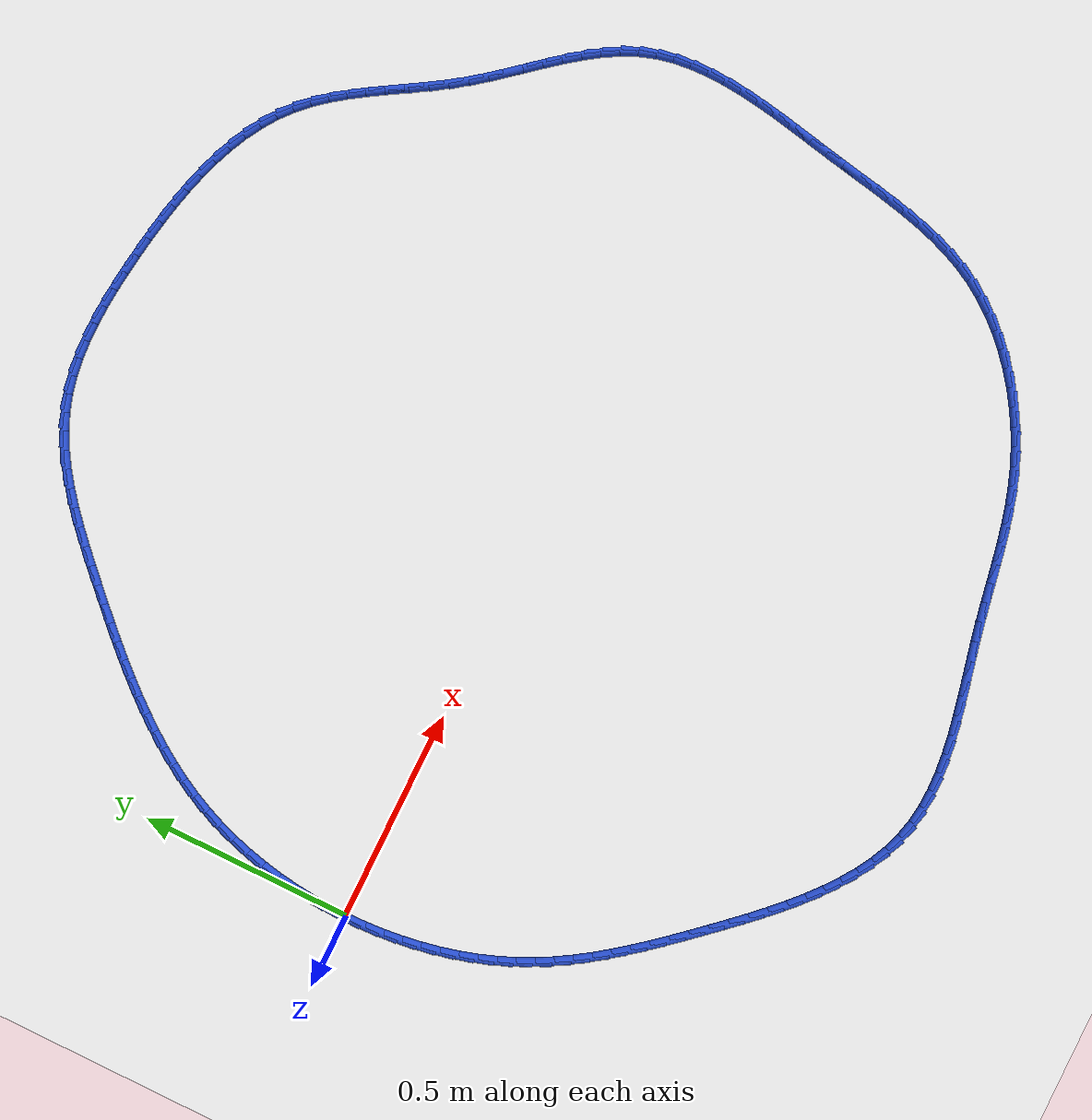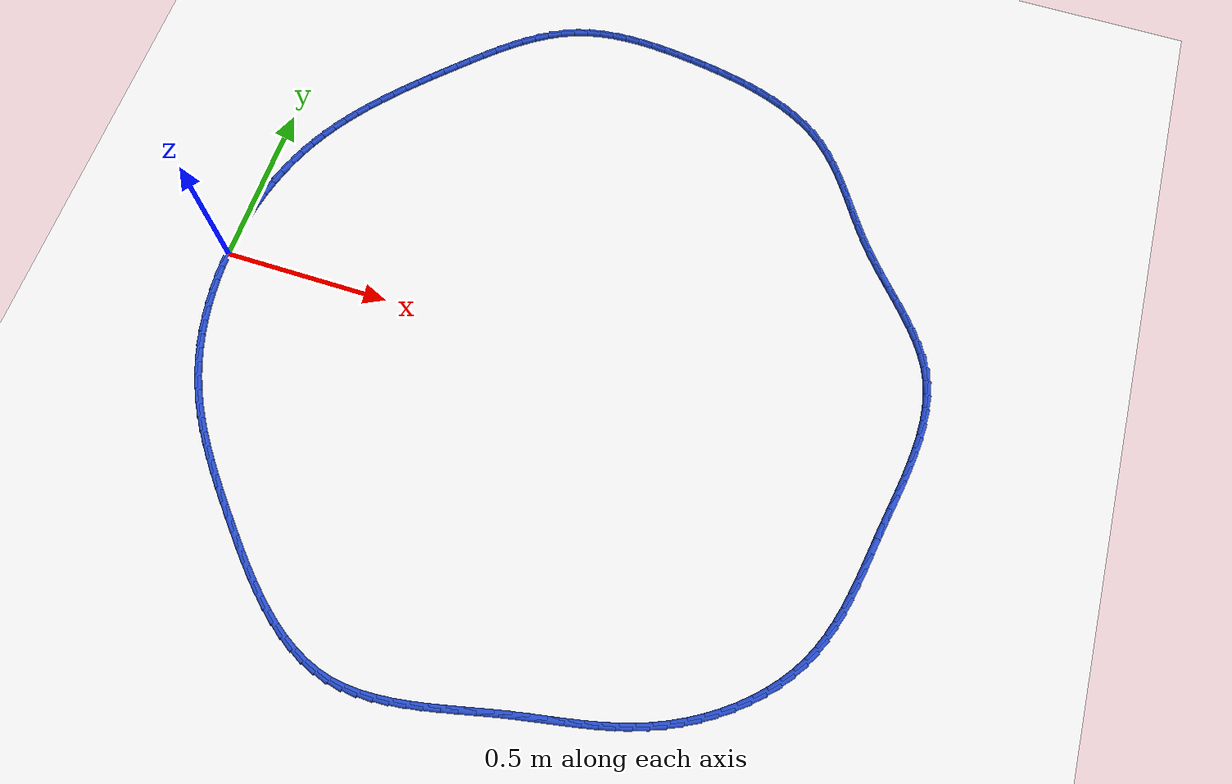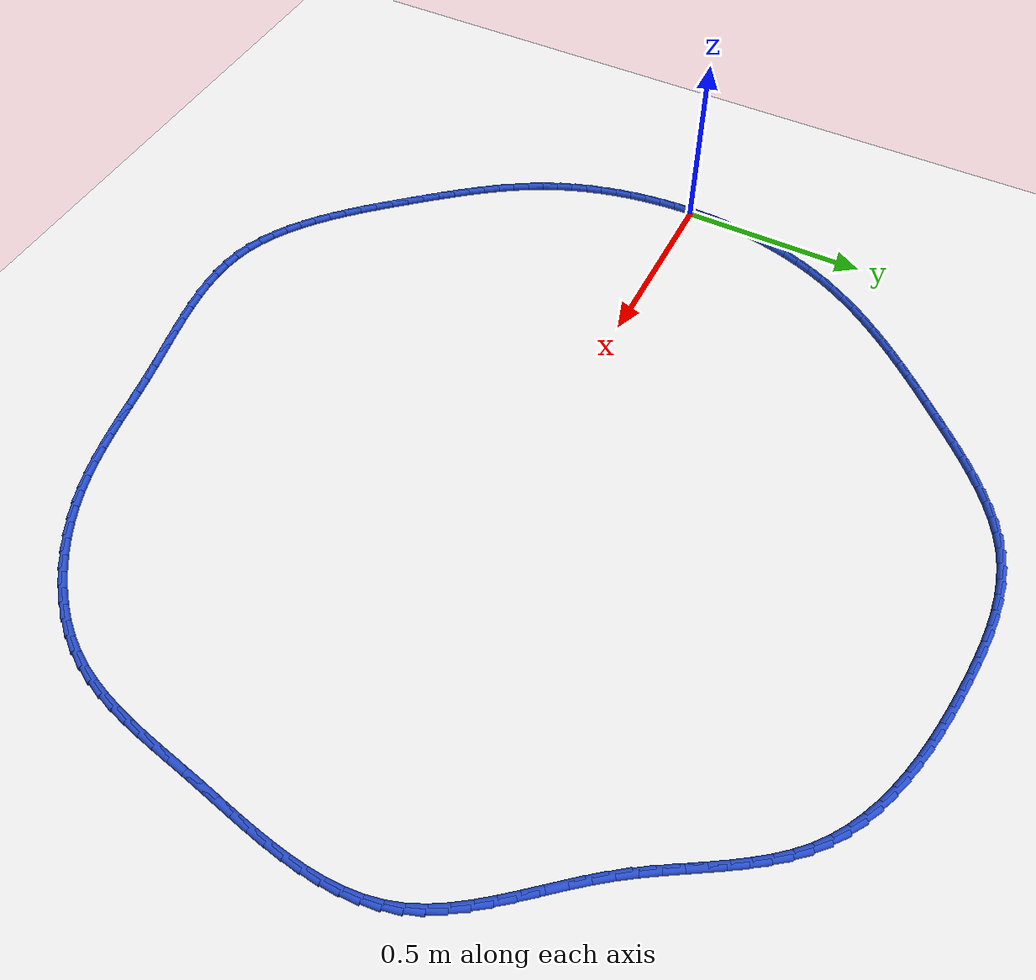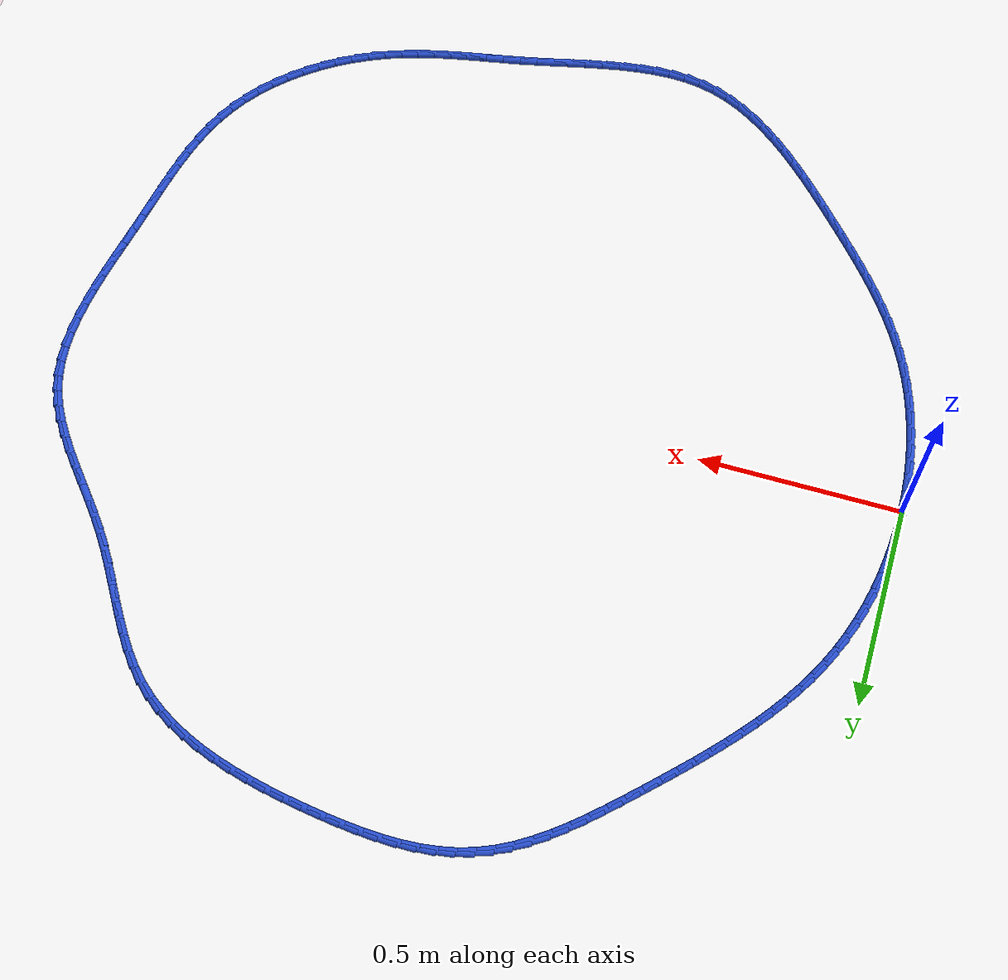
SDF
<sdf version="1.6">
 <world name="default">
  <light name="sun" type="directional">
   <pose>0 0 10 0 -0 0</pose>
   <diffuse>0.8 0.8 0.8 1</diffuse>
   <specular>0.2 0.2 0.2 1</specular>
   <attenuation>
    <range>1000</range>
    <constant>0.9</constant>
    <linear>0.01</linear>
    <quadratic>0.001</quadratic>
   </attenuation>
   <direction>-0.5 0.1 -0.9</direction>
  </light>
  <model name="ground_plane">
   <static>1</static>
   <link name="link">
    <collision name="collision">
     <geometry><plane><normal>0 0 1</normal><size>100 100</size></plane></geometry>
     <surface><friction><ode><mu>100</mu><mu2>50</mu2></ode></friction></surface>
    </collision>
    <visual name="visual">
     <cast_shadows>0</cast_shadows>
     <geometry><plane><normal>0 0 1</normal><size>100 100</size></plane></geometry>
     <material>
      <script><uri>file://media/materials/scripts/gazebo.material</uri><name>Gazebo/WhiteGlow</name></script>
     </material>
    </visual>
   </link>
  </model>
  <gravity>0 0 -9.8</gravity>
  <magnetic_field>6e-06 2.3e-05 -4.2e-05</magnetic_field>
  <atmosphere type="adiabatic"/>
  <physics name="default_physics" default="0" type="ode">
   <max_step_size>0.001</max_step_size>
   <real_time_factor>1</real_time_factor>
   <real_time_update_rate>1000</real_time_update_rate>
  </physics>
  <scene><ambient>0.4 0.4 0.4 1</ambient><background>0.7 0.7 0.7 1</background><shadows>1</shadows></scene>
  <spherical_coordinates>
   <surface_model>EARTH_WGS84</surface_model>
   <latitude_deg>0</latitude_deg>
   <longitude_deg>0</longitude_deg>
   <elevation>0</elevation>
   <heading_deg>0</heading_deg>
  </spherical_coordinates>
  <model name="line">
   <link name="link_0">
    <pose>-3.8163916471489756e-17 5.551115123125783e-17 0.01 0 1.57 1.5495764687321787</pose>
    <collision name="collision">
     <geometry><cylinder><radius>0.01</radius><length>0.08</length></cylinder></geometry>
    </collision>
    <visual name="visual">
     <material>
      <script><name>Gazebo/Blue</name><uri>file://media/materials/scripts/gazebo.material</uri></script>
     </material>
     <geometry><cylinder><radius>0.01</radius><length>0.08</length></cylinder></geometry>
    </visual>
   </link>
   <link name="link_1">
    <pose>0.0009493556558560391 0.04473230480929939 0.01 0 1.57 1.5074194958298273</pose>
    <collision name="collision">
     <geometry><cylinder><radius>0.01</radius><length>0.08</length></cylinder></geometry>
    </collision>
    <visual name="visual">
     <material>
      <script><name>Gazebo/Blue</name><uri>file://media/materials/scripts/gazebo.material</uri></script>
     </material>
     <geometry><cylinder><radius>0.01</radius><length>0.08</length></cylinder></geometry>
    </visual>
   </link>
   <link name="link_2">
    <pose>0.0037793473395203838 0.08932591453530903 0.01 0 1.57 1.4645779964148935</pose>
    <collision name="collision">
     <geometry><cylinder><radius>0.01</radius><length>0.08</length></cylinder></geometry>
    </collision>
    <visual name="visual">
     <material>
      <script><name>Gazebo/Blue</name><uri>file://media/materials/scripts/gazebo.material</uri></script>
     </material>
     <geometry><cylinder><radius>0.01</radius><length>0.08</length></cylinder></geometry>
    </visual>
   </link>
   <link name="link_3">
    <pose>0.008506043564901623 0.13365825123345812 0.01 0 1.57 1.4208562728678937</pose>
    <collision name="collision">
     <geometry><cylinder><radius>0.01</radius><length>0.08</length></cylinder></geometry>
    </collision>
    <visual name="visual">
     <material>
      <script><name>Gazebo/Blue</name><uri>file://media/materials/scripts/gazebo.material</uri></script>
     </material>
     <geometry><cylinder><radius>0.01</radius><length>0.08</length></cylinder></geometry>
    </visual>
   </link>
   <link name="link_4">
    <pose>0.015145512845908388 0.1776067369591758 0.01 0 1.57 1.3760604572505393</pose>
    <collision name="collision">
     <geometry><cylinder><radius>0.01</radius><length>0.08</length></cylinder></geometry>
    </collision>
    <visual name="visual">
     <material>
      <script><name>Gazebo/Blue</name><uri>file://media/materials/scripts/gazebo.material</uri></script>
     </material>
     <geometry><cylinder><radius>0.01</radius><length>0.08</length></cylinder></geometry>
    </visual>
   </link>
   <link name="link_5">
    <pose>0.023713823696449313 0.2210487937678912 0.01 0 1.57 1.3299997670428898</pose>
    <collision name="collision">
     <geometry><cylinder><radius>0.01</radius><length>0.08</length></cylinder></geometry>
    </collision>
    <visual name="visual">
     <material>
      <script><name>Gazebo/Blue</name><uri>file://media/materials/scripts/gazebo.material</uri></script>
     </material>
     <geometry><cylinder><radius>0.01</radius><length>0.08</length></cylinder></geometry>
    </visual>
   </link>
   <link name="link_6">
    <pose>0.03422704463043302 0.26386184371503346 0.01 0 1.57 1.2824886110037068</pose>
    <collision name="collision">
     <geometry><cylinder><radius>0.01</radius><length>0.08</length></cylinder></geometry>
    </collision>
    <visual name="visual">
     <material>
      <script><name>Gazebo/Blue</name><uri>file://media/materials/scripts/gazebo.material</uri></script>
     </material>
     <geometry><cylinder><radius>0.01</radius><length>0.08</length></cylinder></geometry>
    </visual>
   </link>
   <link name="link_7">
    <pose>0.04670124416176816 0.3059233088560316 0.01 0 1.57 1.233349735007347</pose>
    <collision name="collision">
     <geometry><cylinder><radius>0.01</radius><length>0.08</length></cylinder></geometry>
    </collision>
    <visual name="visual">
     <material>
      <script><name>Gazebo/Blue</name><uri>file://media/materials/scripts/gazebo.material</uri></script>
     </material>
     <geometry><cylinder><radius>0.01</radius><length>0.08</length></cylinder></geometry>
    </visual>
   </link>
   <link name="link_8">
    <pose>0.061152490804363364 0.3471106112463149 0.01 0 1.57 1.1824185937702345</pose>
    <collision name="collision">
     <geometry><cylinder><radius>0.01</radius><length>0.08</length></cylinder></geometry>
    </collision>
    <visual name="visual">
     <material>
      <script><name>Gazebo/Blue</name><uri>file://media/materials/scripts/gazebo.material</uri></script>
     </material>
     <geometry><cylinder><radius>0.01</radius><length>0.08</length></cylinder></geometry>
    </visual>
   </link>
   <link name="link_9">
    <pose>0.07759685307212726 0.3873011729413125 0.01 0 1.57 1.1296678207322062</pose>
    <collision name="collision">
     <geometry><cylinder><radius>0.01</radius><length>0.08</length></cylinder></geometry>
    </collision>
    <visual name="visual">
     <material>
      <script><name>Gazebo/Blue</name><uri>file://media/materials/scripts/gazebo.material</uri></script>
     </material>
     <geometry><cylinder><radius>0.01</radius><length>0.08</length></cylinder></geometry>
    </visual>
   </link>
   <link name="link_10">
    <pose>0.09604696405465303 0.4263771547645984 0.01 0 1.57 1.0777235332900583</pose>
    <collision name="collision">
     <geometry><cylinder><radius>0.01</radius><length>0.08</length></cylinder></geometry>
    </collision>
    <visual name="visual">
     <material>
      <script><name>Gazebo/Blue</name><uri>file://media/materials/scripts/gazebo.material</uri></script>
     </material>
     <geometry><cylinder><radius>0.01</radius><length>0.08</length></cylinder></geometry>
    </visual>
   </link>
   <link name="link_11">
    <pose>0.11643874522814841 0.464326532285321 0.01 0 1.57 1.0294805212100286</pose>
    <collision name="collision">
     <geometry><cylinder><radius>0.01</radius><length>0.08</length></cylinder></geometry>
    </collision>
    <visual name="visual">
     <material>
      <script><name>Gazebo/Blue</name><uri>file://media/materials/scripts/gazebo.material</uri></script>
     </material>
     <geometry><cylinder><radius>0.01</radius><length>0.08</length></cylinder></geometry>
    </visual>
   </link>
   <link name="link_12">
    <pose>0.13863266457528123 0.5012413603882517 0.01 0 1.57 0.9853215591011278</pose>
    <collision name="collision">
     <geometry><cylinder><radius>0.01</radius><length>0.08</length></cylinder></geometry>
    </collision>
    <visual name="visual">
     <material>
      <script><name>Gazebo/Blue</name><uri>file://media/materials/scripts/gazebo.material</uri></script>
     </material>
     <geometry><cylinder><radius>0.01</radius><length>0.08</length></cylinder></geometry>
    </visual>
   </link>
   <link name="link_13">
    <pose>0.16248600629994367 0.5372180856105638 0.01 0 1.57 0.9454100412644546</pose>
    <collision name="collision">
     <geometry><cylinder><radius>0.01</radius><length>0.08</length></cylinder></geometry>
    </collision>
    <visual name="visual">
     <material>
      <script><name>Gazebo/Blue</name><uri>file://media/materials/scripts/gazebo.material</uri></script>
     </material>
     <geometry><cylinder><radius>0.01</radius><length>0.08</length></cylinder></geometry>
    </visual>
   </link>
   <link name="link_14">
    <pose>0.1878560546060279 0.5723531544894301 0.01 0 1.57 0.9098189130626636</pose>
    <collision name="collision">
     <geometry><cylinder><radius>0.01</radius><length>0.08</length></cylinder></geometry>
    </collision>
    <visual name="visual">
     <material>
      <script><name>Gazebo/Blue</name><uri>file://media/materials/scripts/gazebo.material</uri></script>
     </material>
     <geometry><cylinder><radius>0.01</radius><length>0.08</length></cylinder></geometry>
    </visual>
   </link>
   <link name="link_15">
    <pose>0.21460009369742594 0.6067430135620231 0.01 0 1.57 0.8785515798164789</pose>
    <collision name="collision">
     <geometry><cylinder><radius>0.01</radius><length>0.08</length></cylinder></geometry>
    </collision>
    <visual name="visual">
     <material>
      <script><name>Gazebo/Blue</name><uri>file://media/materials/scripts/gazebo.material</uri></script>
     </material>
     <geometry><cylinder><radius>0.01</radius><length>0.08</length></cylinder></geometry>
    </visual>
   </link>
   <link name="link_16">
    <pose>0.2425754077780301 0.6404841093655161 0.01 0 1.57 0.8515621695666951</pose>
    <collision name="collision">
     <geometry><cylinder><radius>0.01</radius><length>0.08</length></cylinder></geometry>
    </collision>
    <visual name="visual">
     <material>
      <script><name>Gazebo/Blue</name><uri>file://media/materials/scripts/gazebo.material</uri></script>
     </material>
     <geometry><cylinder><radius>0.01</radius><length>0.08</length></cylinder></geometry>
    </visual>
   </link>
   <link name="link_17">
    <pose>0.27163928105173246 0.6736728884370818 0.01 0 1.57 0.828773526532668</pose>
    <collision name="collision">
     <geometry><cylinder><radius>0.01</radius><length>0.08</length></cylinder></geometry>
    </collision>
    <visual name="visual">
     <material>
      <script><name>Gazebo/Blue</name><uri>file://media/materials/scripts/gazebo.material</uri></script>
     </material>
     <geometry><cylinder><radius>0.01</radius><length>0.08</length></cylinder></geometry>
    </visual>
   </link>
   <link name="link_18">
    <pose>0.30164899772242526 0.7064057973138934 0.01 0 1.57 0.8100921711703246</pose>
    <collision name="collision">
     <geometry><cylinder><radius>0.01</radius><length>0.08</length></cylinder></geometry>
    </collision>
    <visual name="visual">
     <material>
      <script><name>Gazebo/Blue</name><uri>file://media/materials/scripts/gazebo.material</uri></script>
     </material>
     <geometry><cylinder><radius>0.01</radius><length>0.08</length></cylinder></geometry>
    </visual>
   </link>
   <link name="link_19">
    <pose>0.3324618419940004 0.7387792825331232 0.01 0 1.57 0.7954200722240594</pose>
    <collision name="collision">
     <geometry><cylinder><radius>0.01</radius><length>0.08</length></cylinder></geometry>
    </collision>
    <visual name="visual">
     <material>
      <script><name>Gazebo/Blue</name><uri>file://media/materials/scripts/gazebo.material</uri></script>
     </material>
     <geometry><cylinder><radius>0.01</radius><length>0.08</length></cylinder></geometry>
    </visual>
   </link>
   <link name="link_20">
    <pose>0.36393509807035024 0.7708897906319445 0.01 0 1.57 0.7846634388693724</pose>
    <collision name="collision">
     <geometry><cylinder><radius>0.01</radius><length>0.08</length></cylinder></geometry>
    </collision>
    <visual name="visual">
     <material>
      <script><name>Gazebo/Blue</name><uri>file://media/materials/scripts/gazebo.material</uri></script>
     </material>
     <geometry><cylinder><radius>0.01</radius><length>0.08</length></cylinder></geometry>
    </visual>
   </link>
   <link name="link_21">
    <pose>0.3959260501553671 0.8028337681475304 0.01 0 1.57 0.7777389084033097</pose>
    <collision name="collision">
     <geometry><cylinder><radius>0.01</radius><length>0.08</length></cylinder></geometry>
    </collision>
    <visual name="visual">
     <material>
      <script><name>Gazebo/Blue</name><uri>file://media/materials/scripts/gazebo.material</uri></script>
     </material>
     <geometry><cylinder><radius>0.01</radius><length>0.08</length></cylinder></geometry>
    </visual>
   </link>
   <link name="link_22">
    <pose>0.42829198245294275 0.8347076616170532 0.01 0 1.57 0.7726883913819333</pose>
    <collision name="collision">
     <geometry><cylinder><radius>0.01</radius><length>0.08</length></cylinder></geometry>
    </collision>
    <visual name="visual">
     <material>
      <script><name>Gazebo/Blue</name><uri>file://media/materials/scripts/gazebo.material</uri></script>
     </material>
     <geometry><cylinder><radius>0.01</radius><length>0.08</length></cylinder></geometry>
    </visual>
   </link>
   <link name="link_23">
    <pose>0.460930610907944 0.8665269998942474 0.01 0 1.57 0.7611196370617994</pose>
    <collision name="collision">
     <geometry><cylinder><radius>0.01</radius><length>0.08</length></cylinder></geometry>
    </collision>
    <visual name="visual">
     <material>
      <script><name>Gazebo/Blue</name><uri>file://media/materials/scripts/gazebo.material</uri></script>
     </material>
     <geometry><cylinder><radius>0.01</radius><length>0.08</length></cylinder></geometry>
    </visual>
   </link>
   <link name="link_24">
    <pose>0.49391803056233474 0.8979503145093751 0.01 0 1.57 0.7405549830315604</pose>
    <collision name="collision">
     <geometry><cylinder><radius>0.01</radius><length>0.08</length></cylinder></geometry>
    </collision>
    <visual name="visual">
     <material>
      <script><name>Gazebo/Blue</name><uri>file://media/materials/scripts/gazebo.material</uri></script>
     </material>
     <geometry><cylinder><radius>0.01</radius><length>0.08</length></cylinder></geometry>
    </visual>
   </link>
   <link name="link_25">
    <pose>0.5273795141642877 0.9285377156542325 0.01 0 1.57 0.7105964394991345</pose>
    <collision name="collision">
     <geometry><cylinder><radius>0.01</radius><length>0.08</length></cylinder></geometry>
    </collision>
    <visual name="visual">
     <material>
      <script><name>Gazebo/Blue</name><uri>file://media/materials/scripts/gazebo.material</uri></script>
     </material>
     <geometry><cylinder><radius>0.01</radius><length>0.08</length></cylinder></geometry>
    </visual>
   </link>
   <link name="link_26">
    <pose>0.5614403360161417 0.9578493104102005 0.01 0 1.57 0.6706529719863801</pose>
    <collision name="collision">
     <geometry><cylinder><radius>0.01</radius><length>0.08</length></cylinder></geometry>
    </collision>
    <visual name="visual">
     <material>
      <script><name>Gazebo/Blue</name><uri>file://media/materials/scripts/gazebo.material</uri></script>
     </material>
     <geometry><cylinder><radius>0.01</radius><length>0.08</length></cylinder></geometry>
    </visual>
   </link>
   <link name="link_27">
    <pose>0.5962257704202353 0.9854452058586594 0.01 0 1.57 0.6199986322860451</pose>
    <collision name="collision">
     <geometry><cylinder><radius>0.01</radius><length>0.08</length></cylinder></geometry>
    </collision>
    <visual name="visual">
     <material>
      <script><name>Gazebo/Blue</name><uri>file://media/materials/scripts/gazebo.material</uri></script>
     </material>
     <geometry><cylinder><radius>0.01</radius><length>0.08</length></cylinder></geometry>
    </visual>
   </link>
   <link name="link_28">
    <pose>0.6318610916789068 1.0108855090809892 0.01 0 1.57 0.5578774738603502</pose>
    <collision name="collision">
     <geometry><cylinder><radius>0.01</radius><length>0.08</length></cylinder></geometry>
    </collision>
    <visual name="visual">
     <material>
      <script><name>Gazebo/Blue</name><uri>file://media/materials/scripts/gazebo.material</uri></script>
     </material>
     <geometry><cylinder><radius>0.01</radius><length>0.08</length></cylinder></geometry>
    </visual>
   </link>
   <link name="link_29">
    <pose>0.6684715740944953 1.033730327158571 0.01 0 1.57 0.4836799661511655</pose>
    <collision name="collision">
     <geometry><cylinder><radius>0.01</radius><length>0.08</length></cylinder></geometry>
    </collision>
    <visual name="visual">
     <material>
      <script><name>Gazebo/Blue</name><uri>file://media/materials/scripts/gazebo.material</uri></script>
     </material>
     <geometry><cylinder><radius>0.01</radius><length>0.08</length></cylinder></geometry>
    </visual>
   </link>
   <link name="link_30">
    <pose>0.7061824919693394 1.053539767172785 0.01 0 1.57 0.3972084316619674</pose>
    <collision name="collision">
     <geometry><cylinder><radius>0.01</radius><length>0.08</length></cylinder></geometry>
    </collision>
    <visual name="visual">
     <material>
      <script><name>Gazebo/Blue</name><uri>file://media/materials/scripts/gazebo.material</uri></script>
     </material>
     <geometry><cylinder><radius>0.01</radius><length>0.08</length></cylinder></geometry>
    </visual>
   </link>
   <link name="link_31">
    <pose>0.7451191196057775 1.0698739362050118 0.01 0 1.57 0.30150304699337</pose>
    <collision name="collision">
     <geometry><cylinder><radius>0.01</radius><length>0.08</length></cylinder></geometry>
    </collision>
    <visual name="visual">
     <material>
      <script><name>Gazebo/Blue</name><uri>file://media/materials/scripts/gazebo.material</uri></script>
     </material>
     <geometry><cylinder><radius>0.01</radius><length>0.08</length></cylinder></geometry>
    </visual>
   </link>
   <link name="link_32">
    <pose>0.7853728100791115 1.0823921854087726 0.01 0 1.57 0.21109179228786562</pose>
    <collision name="collision">
     <geometry><cylinder><radius>0.01</radius><length>0.08</length></cylinder></geometry>
    </collision>
    <visual name="visual">
     <material>
      <script><name>Gazebo/Blue</name><uri>file://media/materials/scripts/gazebo.material</uri></script>
     </material>
     <geometry><cylinder><radius>0.01</radius><length>0.08</length></cylinder></geometry>
    </visual>
   </link>
   <link name="link_33">
    <pose>0.826854710893519 1.0912810972986875 0.01 0 1.57 0.13129713475901295</pose>
    <collision name="collision">
     <geometry><cylinder><radius>0.01</radius><length>0.08</length></cylinder></geometry>
    </collision>
    <visual name="visual">
     <material>
      <script><name>Gazebo/Blue</name><uri>file://media/materials/scripts/gazebo.material</uri></script>
     </material>
     <geometry><cylinder><radius>0.01</radius><length>0.08</length></cylinder></geometry>
    </visual>
   </link>
   <link name="link_34">
    <pose>0.8694163602686742 1.096901654570277 0.01 0 1.57 0.06230407708794974</pose>
    <collision name="collision">
     <geometry><cylinder><radius>0.01</radius><length>0.08</length></cylinder></geometry>
    </collision>
    <visual name="visual">
     <material>
      <script><name>Gazebo/Blue</name><uri>file://media/materials/scripts/gazebo.material</uri></script>
     </material>
     <geometry><cylinder><radius>0.01</radius><length>0.08</length></cylinder></geometry>
    </visual>
   </link>
   <link name="link_35">
    <pose>0.9129092583957099 1.0996149511799893 0.01 0 1.57 0.0037747412302158163</pose>
    <collision name="collision">
     <geometry><cylinder><radius>0.01</radius><length>0.08</length></cylinder></geometry>
    </collision>
    <visual name="visual">
     <material>
      <script><name>Gazebo/Blue</name><uri>file://media/materials/scripts/gazebo.material</uri></script>
     </material>
     <geometry><cylinder><radius>0.01</radius><length>0.08</length></cylinder></geometry>
    </visual>
   </link>
   <link name="link_36">
    <pose>0.9571849054657594 1.0997820810842729 0.01 0 1.57 -0.04490294101807372</pose>
    <collision name="collision">
     <geometry><cylinder><radius>0.01</radius><length>0.08</length></cylinder></geometry>
    </collision>
    <visual name="visual">
     <material>
      <script><name>Gazebo/Blue</name><uri>file://media/materials/scripts/gazebo.material</uri></script>
     </material>
     <geometry><cylinder><radius>0.01</radius><length>0.08</length></cylinder></geometry>
    </visual>
   </link>
   <link name="link_37">
    <pose>1.0020948016699558 1.0977641382395769 0.01 0 1.57 -0.08443074528327679</pose>
    <collision name="collision">
     <geometry><cylinder><radius>0.01</radius><length>0.08</length></cylinder></geometry>
    </collision>
    <visual name="visual">
     <material>
      <script><name>Gazebo/Blue</name><uri>file://media/materials/scripts/gazebo.material</uri></script>
     </material>
     <geometry><cylinder><radius>0.01</radius><length>0.08</length></cylinder></geometry>
    </visual>
   </link>
   <link name="link_38">
    <pose>1.0474904471994326 1.0939222166023497 0.01 0 1.57 -0.11547934512570122</pose>
    <collision name="collision">
     <geometry><cylinder><radius>0.01</radius><length>0.08</length></cylinder></geometry>
    </collision>
    <visual name="visual">
     <material>
      <script><name>Gazebo/Blue</name><uri>file://media/materials/scripts/gazebo.material</uri></script>
     </material>
     <geometry><cylinder><radius>0.01</radius><length>0.08</length></cylinder></geometry>
    </visual>
   </link>
   <link name="link_39">
    <pose>1.0932233422453226 1.0886174101290398 0.01 0 1.57 -0.13863119221207096</pose>
    <collision name="collision">
     <geometry><cylinder><radius>0.01</radius><length>0.08</length></cylinder></geometry>
    </collision>
    <visual name="visual">
     <material>
      <script><name>Gazebo/Blue</name><uri>file://media/materials/scripts/gazebo.material</uri></script>
     </material>
     <geometry><cylinder><radius>0.01</radius><length>0.08</length></cylinder></geometry>
    </visual>
   </link>
   <link name="link_40">
    <pose>1.139144859240316 1.0822101566301021 0.01 0 1.57 -0.15773992628443598</pose>
    <collision name="collision">
     <geometry><cylinder><radius>0.01</radius><length>0.08</length></cylinder></geometry>
    </collision>
    <visual name="visual">
     <material>
      <script><name>Gazebo/Blue</name><uri>file://media/materials/scripts/gazebo.material</uri></script>
     </material>
     <geometry><cylinder><radius>0.01</radius><length>0.08</length></cylinder></geometry>
    </visual>
   </link>
   <link name="link_41">
    <pose>1.1850758812078432 1.0749043054100256 0.01 0 1.57 -0.18094231287844695</pose>
    <collision name="collision">
     <geometry><cylinder><radius>0.01</radius><length>0.08</length></cylinder></geometry>
    </collision>
    <visual name="visual">
     <material>
      <script><name>Gazebo/Blue</name><uri>file://media/materials/scripts/gazebo.material</uri></script>
     </material>
     <geometry><cylinder><radius>0.01</radius><length>0.08</length></cylinder></geometry>
    </visual>
   </link>
   <link name="link_42">
    <pose>1.2307675120178925 1.0665453317132585 0.01 0 1.57 -0.20965833708193293</pose>
    <collision name="collision">
     <geometry><cylinder><radius>0.01</radius><length>0.08</length></cylinder></geometry>
    </collision>
    <visual name="visual">
     <material>
      <script><name>Gazebo/Blue</name><uri>file://media/materials/scripts/gazebo.material</uri></script>
     </material>
     <geometry><cylinder><radius>0.01</radius><length>0.08</length></cylinder></geometry>
    </visual>
   </link>
   <link name="link_43">
    <pose>1.2759611361246872 1.0569287934906524 0.01 0 1.57 -0.24432821090702156</pose>
    <collision name="collision">
     <geometry><cylinder><radius>0.01</radius><length>0.08</length></cylinder></geometry>
    </collision>
    <visual name="visual">
     <material>
      <script><name>Gazebo/Blue</name><uri>file://media/materials/scripts/gazebo.material</uri></script>
     </material>
     <geometry><cylinder><radius>0.01</radius><length>0.08</length></cylinder></geometry>
    </visual>
   </link>
   <link name="link_44">
    <pose>1.32039813798245 1.0458502486930576 0.01 0 1.57 -0.28549783791102956</pose>
    <collision name="collision">
     <geometry><cylinder><radius>0.01</radius><length>0.08</length></cylinder></geometry>
    </collision>
    <visual name="visual">
     <material>
      <script><name>Gazebo/Blue</name><uri>file://media/materials/scripts/gazebo.material</uri></script>
     </material>
     <geometry><cylinder><radius>0.01</radius><length>0.08</length></cylinder></geometry>
    </visual>
   </link>
   <link name="link_45">
    <pose>1.3638199020454056 1.0331052552713258 0.01 0 1.57 -0.33379978116029424</pose>
    <collision name="collision">
     <geometry><cylinder><radius>0.01</radius><length>0.08</length></cylinder></geometry>
    </collision>
    <visual name="visual">
     <material>
      <script><name>Gazebo/Blue</name><uri>file://media/materials/scripts/gazebo.material</uri></script>
     </material>
     <geometry><cylinder><radius>0.01</radius><length>0.08</length></cylinder></geometry>
    </visual>
   </link>
   <link name="link_46">
    <pose>1.4059678127677755 1.0184893711763083 0.01 0 1.57 -0.3899165864248529</pose>
    <collision name="collision">
     <geometry><cylinder><radius>0.01</radius><length>0.08</length></cylinder></geometry>
    </collision>
    <visual name="visual">
     <material>
      <script><name>Gazebo/Blue</name><uri>file://media/materials/scripts/gazebo.material</uri></script>
     </material>
     <geometry><cylinder><radius>0.01</radius><length>0.08</length></cylinder></geometry>
    </visual>
   </link>
   <link name="link_47">
    <pose>1.446583254603784 1.001798154358856 0.01 0 1.57 -0.4545154171378272</pose>
    <collision name="collision">
     <geometry><cylinder><radius>0.01</radius><length>0.08</length></cylinder></geometry>
    </collision>
    <visual name="visual">
     <material>
      <script><name>Gazebo/Blue</name><uri>file://media/materials/scripts/gazebo.material</uri></script>
     </material>
     <geometry><cylinder><radius>0.01</radius><length>0.08</length></cylinder></geometry>
    </visual>
   </link>
   <link name="link_48">
    <pose>1.485407612007653 0.9828271627698199 0.01 0 1.57 -0.5281419042610613</pose>
    <collision name="collision">
     <geometry><cylinder><radius>0.01</radius><length>0.08</length></cylinder></geometry>
    </collision>
    <visual name="visual">
     <material>
      <script><name>Gazebo/Blue</name><uri>file://media/materials/scripts/gazebo.material</uri></script>
     </material>
     <geometry><cylinder><radius>0.01</radius><length>0.08</length></cylinder></geometry>
    </visual>
   </link>
   <link name="link_49">
    <pose>1.5221822694336062 0.9613719543600509 0.01 0 1.57 -0.6110652470176426</pose>
    <collision name="collision">
     <geometry><cylinder><radius>0.01</radius><length>0.08</length></cylinder></geometry>
    </collision>
    <visual name="visual">
     <material>
      <script><name>Gazebo/Blue</name><uri>file://media/materials/scripts/gazebo.material</uri></script>
     </material>
     <geometry><cylinder><radius>0.01</radius><length>0.08</length></cylinder></geometry>
    </visual>
   </link>
   <link name="link_50">
    <pose>1.5566486113358675 0.9372280870804003 0.01 0 1.57 -0.7030805078337105</pose>
    <collision name="collision">
     <geometry><cylinder><radius>0.01</radius><length>0.08</length></cylinder></geometry>
    </collision>
    <visual name="visual">
     <material>
      <script><name>Gazebo/Blue</name><uri>file://media/materials/scripts/gazebo.material</uri></script>
     </material>
     <geometry><cylinder><radius>0.01</radius><length>0.08</length></cylinder></geometry>
    </visual>
   </link>
   <link name="link_51">
    <pose>1.588548049117006 0.9101911421825237 0.01 0 1.57 -0.798433416173682</pose>
    <collision name="collision">
     <geometry><cylinder><radius>0.01</radius><length>0.08</length></cylinder></geometry>
    </collision>
    <visual name="visual">
     <material>
      <script><name>Gazebo/Blue</name><uri>file://media/materials/scripts/gazebo.material</uri></script>
     </material>
     <geometry><cylinder><radius>0.01</radius><length>0.08</length></cylinder></geometry>
    </visual>
   </link>
   <link name="link_52">
    <pose>1.6177766525851347 0.8801904258263135 0.01 0 1.57 -0.8793918547365092</pose>
    <collision name="collision">
     <geometry><cylinder><radius>0.01</radius><length>0.08</length></cylinder></geometry>
    </collision>
    <visual name="visual">
     <material>
      <script><name>Gazebo/Blue</name><uri>file://media/materials/scripts/gazebo.material</uri></script>
     </material>
     <geometry><cylinder><radius>0.01</radius><length>0.08</length></cylinder></geometry>
    </visual>
   </link>
   <link name="link_53">
    <pose>1.6447488793283103 0.8476034665496271 0.01 0 1.57 -0.9419798324300654</pose>
    <collision name="collision">
     <geometry><cylinder><radius>0.01</radius><length>0.08</length></cylinder></geometry>
    </collision>
    <visual name="visual">
     <material>
      <script><name>Gazebo/Blue</name><uri>file://media/materials/scripts/gazebo.material</uri></script>
     </material>
     <geometry><cylinder><radius>0.01</radius><length>0.08</length></cylinder></geometry>
    </visual>
   </link>
   <link name="link_54">
    <pose>1.6699876749960751 0.812901596754496 0.01 0 1.57 -0.9866510703602411</pose>
    <collision name="collision">
     <geometry><cylinder><radius>0.01</radius><length>0.08</length></cylinder></geometry>
    </collision>
    <visual name="visual">
     <material>
      <script><name>Gazebo/Blue</name><uri>file://media/materials/scripts/gazebo.material</uri></script>
     </material>
     <geometry><cylinder><radius>0.01</radius><length>0.08</length></cylinder></geometry>
    </visual>
   </link>
   <link name="link_55">
    <pose>1.6940159852379704 0.7765561488429531 0.01 0 1.57 -1.014265651700936</pose>
    <collision name="collision">
     <geometry><cylinder><radius>0.01</radius><length>0.08</length></cylinder></geometry>
    </collision>
    <visual name="visual">
     <material>
      <script><name>Gazebo/Blue</name><uri>file://media/materials/scripts/gazebo.material</uri></script>
     </material>
     <geometry><cylinder><radius>0.01</radius><length>0.08</length></cylinder></geometry>
    </visual>
   </link>
   <link name="link_56">
    <pose>1.7173567557035383 0.7390384552170293 0.01 0 1.57 -1.0256763257706387</pose>
    <collision name="collision">
     <geometry><cylinder><radius>0.01</radius><length>0.08</length></cylinder></geometry>
    </collision>
    <visual name="visual">
     <material>
      <script><name>Gazebo/Blue</name><uri>file://media/materials/scripts/gazebo.material</uri></script>
     </material>
     <geometry><cylinder><radius>0.01</radius><length>0.08</length></cylinder></geometry>
    </visual>
   </link>
   <link name="link_57">
    <pose>1.7405329320423215 0.7008198482787569 0.01 0 1.57 -1.021519822923509</pose>
    <collision name="collision">
     <geometry><cylinder><radius>0.01</radius><length>0.08</length></cylinder></geometry>
    </collision>
    <visual name="visual">
     <material>
      <script><name>Gazebo/Blue</name><uri>file://media/materials/scripts/gazebo.material</uri></script>
     </material>
     <geometry><cylinder><radius>0.01</radius><length>0.08</length></cylinder></geometry>
    </visual>
   </link>
   <link name="link_58">
    <pose>1.7640674599038613 0.6623716604301668 0.01 0 1.57 -1.0021573415300908</pose>
    <collision name="collision">
     <geometry><cylinder><radius>0.01</radius><length>0.08</length></cylinder></geometry>
    </collision>
    <visual name="visual">
     <material>
      <script><name>Gazebo/Blue</name><uri>file://media/materials/scripts/gazebo.material</uri></script>
     </material>
     <geometry><cylinder><radius>0.01</radius><length>0.08</length></cylinder></geometry>
    </visual>
   </link>
   <link name="link_59">
    <pose>1.788483284937699 0.6241652240732917 0.01 0 1.57 -0.9677253586184543</pose>
    <collision name="collision">
     <geometry><cylinder><radius>0.01</radius><length>0.08</length></cylinder></geometry>
    </collision>
    <visual name="visual">
     <material>
      <script><name>Gazebo/Blue</name><uri>file://media/materials/scripts/gazebo.material</uri></script>
     </material>
     <geometry><cylinder><radius>0.01</radius><length>0.08</length></cylinder></geometry>
    </visual>
   </link>
   <link name="link_60">
    <pose>1.8143032847248628 0.5866718293719743 0.01 0 1.57 -0.9246000153751803</pose>
    <collision name="collision">
     <geometry><cylinder><radius>0.01</radius><length>0.08</length></cylinder></geometry>
    </collision>
    <visual name="visual">
     <material>
      <script><name>Gazebo/Blue</name><uri>file://media/materials/scripts/gazebo.material</uri></script>
     </material>
     <geometry><cylinder><radius>0.01</radius><length>0.08</length></cylinder></geometry>
    </visual>
   </link>
   <link name="link_61">
    <pose>1.8418037188357868 0.5502097339435496 0.01 0 1.57 -0.8931862985490858</pose>
    <collision name="collision">
     <geometry><cylinder><radius>0.01</radius><length>0.08</length></cylinder></geometry>
    </collision>
    <visual name="visual">
     <material>
      <script><name>Gazebo/Blue</name><uri>file://media/materials/scripts/gazebo.material</uri></script>
     </material>
     <geometry><cylinder><radius>0.01</radius><length>0.08</length></cylinder></geometry>
    </visual>
   </link>
   <link name="link_62">
    <pose>1.8704594964993393 0.5145999377917664 0.01 0 1.57 -0.8773095075462517</pose>
    <collision name="collision">
     <geometry><cylinder><radius>0.01</radius><length>0.08</length></cylinder></geometry>
    </collision>
    <visual name="visual">
     <material>
      <script><name>Gazebo/Blue</name><uri>file://media/materials/scripts/gazebo.material</uri></script>
     </material>
     <geometry><cylinder><radius>0.01</radius><length>0.08</length></cylinder></geometry>
    </visual>
   </link>
   <link name="link_63">
    <pose>1.899583044211797 0.4795626163850056 0.01 0 1.57 -0.8769104631869721</pose>
    <collision name="collision">
     <geometry><cylinder><radius>0.01</radius><length>0.08</length></cylinder></geometry>
    </collision>
    <visual name="visual">
     <material>
      <script><name>Gazebo/Blue</name><uri>file://media/materials/scripts/gazebo.material</uri></script>
     </material>
     <geometry><cylinder><radius>0.01</radius><length>0.08</length></cylinder></geometry>
    </visual>
   </link>
   <link name="link_64">
    <pose>1.9284867884694412 0.44481794519164725 0.01 0 1.57 -0.8923639116627092</pose>
    <collision name="collision">
     <geometry><cylinder><radius>0.01</radius><length>0.08</length></cylinder></geometry>
    </collision>
    <visual name="visual">
     <material>
      <script><name>Gazebo/Blue</name><uri>file://media/materials/scripts/gazebo.material</uri></script>
     </material>
     <geometry><cylinder><radius>0.01</radius><length>0.08</length></cylinder></geometry>
    </visual>
   </link>
   <link name="link_65">
    <pose>1.9564831557685498 0.410086099680072 0.01 0 1.57 -0.924516323252132</pose>
    <collision name="collision">
     <geometry><cylinder><radius>0.01</radius><length>0.08</length></cylinder></geometry>
    </collision>
    <visual name="visual">
     <material>
      <script><name>Gazebo/Blue</name><uri>file://media/materials/scripts/gazebo.material</uri></script>
     </material>
     <geometry><cylinder><radius>0.01</radius><length>0.08</length></cylinder></geometry>
    </visual>
   </link>
   <link name="link_66">
    <pose>1.9828845726054034 0.3750872553186605 0.01 0 1.57 -0.9746238010650542</pose>
    <collision name="collision">
     <geometry><cylinder><radius>0.01</radius><length>0.08</length></cylinder></geometry>
    </collision>
    <visual name="visual">
     <material>
      <script><name>Gazebo/Blue</name><uri>file://media/materials/scripts/gazebo.material</uri></script>
     </material>
     <geometry><cylinder><radius>0.01</radius><length>0.08</length></cylinder></geometry>
    </visual>
   </link>
   <link name="link_67">
    <pose>2.00700346547628 0.33954158757579267 0.01 0 1.57 -1.0441259007853316</pose>
    <collision name="collision">
     <geometry><cylinder><radius>0.01</radius><length>0.08</length></cylinder></geometry>
    </collision>
    <visual name="visual">
     <material>
      <script><name>Gazebo/Blue</name><uri>file://media/materials/scripts/gazebo.material</uri></script>
     </material>
     <geometry><cylinder><radius>0.01</radius><length>0.08</length></cylinder></geometry>
    </visual>
   </link>
   <link name="link_68">
    <pose>2.0281522608774587 0.3031692719198498 0.01 0 1.57 -1.1341467461948769</pose>
    <collision name="collision">
     <geometry><cylinder><radius>0.01</radius><length>0.08</length></cylinder></geometry>
    </collision>
    <visual name="visual">
     <material>
      <script><name>Gazebo/Blue</name><uri>file://media/materials/scripts/gazebo.material</uri></script>
     </material>
     <geometry><cylinder><radius>0.01</radius><length>0.08</length></cylinder></geometry>
    </visual>
   </link>
   <link name="link_69">
    <pose>2.0456433853052194 0.26569048381921223 0.01 0 1.57 -1.2434907560272814</pose>
    <collision name="collision">
     <geometry><cylinder><radius>0.01</radius><length>0.08</length></cylinder></geometry>
    </collision>
    <visual name="visual">
     <material>
      <script><name>Gazebo/Blue</name><uri>file://media/materials/scripts/gazebo.material</uri></script>
     </material>
     <geometry><cylinder><radius>0.01</radius><length>0.08</length></cylinder></geometry>
    </visual>
   </link>
   <link name="link_70">
    <pose>2.0588330752010413 0.22684210070071997 0.01 0 1.57 -1.353787744480869</pose>
    <collision name="collision">
     <geometry><cylinder><radius>0.01</radius><length>0.08</length></cylinder></geometry>
    </collision>
    <visual name="visual">
     <material>
      <script><name>Gazebo/Blue</name><uri>file://media/materials/scripts/gazebo.material</uri></script>
     </material>
     <geometry><cylinder><radius>0.01</radius><length>0.08</length></cylinder></geometry>
    </visual>
   </link>
   <link name="link_71">
    <pose>2.067705580915384 0.18660042193461115 0.01 0 1.57 -1.4506123841829117</pose>
    <collision name="collision">
     <geometry><cylinder><radius>0.01</radius><length>0.08</length></cylinder></geometry>
    </collision>
    <visual name="visual">
     <material>
      <script><name>Gazebo/Blue</name><uri>file://media/materials/scripts/gazebo.material</uri></script>
     </material>
     <geometry><cylinder><radius>0.01</radius><length>0.08</length></cylinder></geometry>
    </visual>
   </link>
   <link name="link_72">
    <pose>2.0727149032273884 0.14512083298927994 0.01 0 1.57 -1.5329492440120065</pose>
    <collision name="collision">
     <geometry><cylinder><radius>0.01</radius><length>0.08</length></cylinder></geometry>
    </collision>
    <visual name="visual">
     <material>
      <script><name>Gazebo/Blue</name><uri>file://media/materials/scripts/gazebo.material</uri></script>
     </material>
     <geometry><cylinder><radius>0.01</radius><length>0.08</length></cylinder></geometry>
    </visual>
   </link>
   <link name="link_73">
    <pose>2.074326361249427 0.10256303429700687 0.01 0 1.57 1.5404193044401566</pose>
    <collision name="collision">
     <geometry><cylinder><radius>0.01</radius><length>0.08</length></cylinder></geometry>
    </collision>
    <visual name="visual">
     <material>
      <script><name>Gazebo/Blue</name><uri>file://media/materials/scripts/gazebo.material</uri></script>
     </material>
     <geometry><cylinder><radius>0.01</radius><length>0.08</length></cylinder></geometry>
    </visual>
   </link>
   <link name="link_74">
    <pose>2.0730052740938687 0.059086726290073055 0.01 0 1.57 1.4853643778064614</pose>
    <collision name="collision">
     <geometry><cylinder><radius>0.01</radius><length>0.08</length></cylinder></geometry>
    </collision>
    <visual name="visual">
     <material>
      <script><name>Gazebo/Blue</name><uri>file://media/materials/scripts/gazebo.material</uri></script>
     </material>
     <geometry><cylinder><radius>0.01</radius><length>0.08</length></cylinder></geometry>
    </visual>
   </link>
   <link name="link_75">
    <pose>2.0692169608730864 0.014851609400759448 0.01 0 1.57 1.4423599203762099</pose>
    <collision name="collision">
     <geometry><cylinder><radius>0.01</radius><length>0.08</length></cylinder></geometry>
    </collision>
    <visual name="visual">
     <material>
      <script><name>Gazebo/Blue</name><uri>file://media/materials/scripts/gazebo.material</uri></script>
     </material>
     <geometry><cylinder><radius>0.01</radius><length>0.08</length></cylinder></geometry>
    </visual>
   </link>
   <link name="link_76">
    <pose>2.063426740699451 -0.029982615938653305 0.01 0 1.57 1.4103534676827447</pose>
    <collision name="collision">
     <geometry><cylinder><radius>0.01</radius><length>0.08</length></cylinder></geometry>
    </collision>
    <visual name="visual">
     <material>
      <script><name>Gazebo/Blue</name><uri>file://media/materials/scripts/gazebo.material</uri></script>
     </material>
     <geometry><cylinder><radius>0.01</radius><length>0.08</length></cylinder></geometry>
    </visual>
   </link>
   <link name="link_77">
    <pose>2.0560999326853326 -0.07525624929588384 0.01 0 1.57 1.388486364912847</pose>
    <collision name="collision">
     <geometry><cylinder><radius>0.01</radius><length>0.08</length></cylinder></geometry>
    </collision>
    <visual name="visual">
     <material>
      <script><name>Gazebo/Blue</name><uri>file://media/materials/scripts/gazebo.material</uri></script>
     </material>
     <geometry><cylinder><radius>0.01</radius><length>0.08</length></cylinder></geometry>
    </visual>
   </link>
   <link name="link_78">
    <pose>2.0477018559431035 -0.1208095902386504 0.01 0 1.57 1.3761526418535677</pose>
    <collision name="collision">
     <geometry><cylinder><radius>0.01</radius><length>0.08</length></cylinder></geometry>
    </collision>
    <visual name="visual">
     <material>
      <script><name>Gazebo/Blue</name><uri>file://media/materials/scripts/gazebo.material</uri></script>
     </material>
     <geometry><cylinder><radius>0.01</radius><length>0.08</length></cylinder></geometry>
    </visual>
   </link>
   <link name="link_79">
    <pose>2.0386978295851352 -0.16648293833467348 0.01 0 1.57 1.3730230821510676</pose>
    <collision name="collision">
     <geometry><cylinder><radius>0.01</radius><length>0.08</length></cylinder></geometry>
    </collision>
    <visual name="visual">
     <material>
      <script><name>Gazebo/Blue</name><uri>file://media/materials/scripts/gazebo.material</uri></script>
     </material>
     <geometry><cylinder><radius>0.01</radius><length>0.08</length></cylinder></geometry>
    </visual>
   </link>
   <link name="link_80">
    <pose>2.0295531727237983 -0.21211659315167058 0.01 0 1.57 1.3789358060772101</pose>
    <collision name="collision">
     <geometry><cylinder><radius>0.01</radius><length>0.08</length></cylinder></geometry>
    </collision>
    <visual name="visual">
     <material>
      <script><name>Gazebo/Blue</name><uri>file://media/materials/scripts/gazebo.material</uri></script>
     </material>
     <geometry><cylinder><radius>0.01</radius><length>0.08</length></cylinder></geometry>
    </visual>
   </link>
   <link name="link_81">
    <pose>2.02072753233871 -0.25755106662509986 0.01 0 1.57 1.3870120859816333</pose>
    <collision name="collision">
     <geometry><cylinder><radius>0.01</radius><length>0.08</length></cylinder></geometry>
    </collision>
    <visual name="visual">
     <material>
      <script><name>Gazebo/Blue</name><uri>file://media/materials/scripts/gazebo.material</uri></script>
     </material>
     <geometry><cylinder><radius>0.01</radius><length>0.08</length></cylinder></geometry>
    </visual>
   </link>
   <link name="link_82">
    <pose>2.0123464358924736 -0.3026393803069979 0.01 0 1.57 1.3863110543281771</pose>
    <collision name="collision">
     <geometry><cylinder><radius>0.01</radius><length>0.08</length></cylinder></geometry>
    </collision>
    <visual name="visual">
     <material>
      <script><name>Gazebo/Blue</name><uri>file://media/materials/scripts/gazebo.material</uri></script>
     </material>
     <geometry><cylinder><radius>0.01</radius><length>0.08</length></cylinder></geometry>
    </visual>
   </link>
   <link name="link_83">
    <pose>2.0040210642558507 -0.3472538131657623 0.01 0 1.57 1.3755993160708306</pose>
    <collision name="collision">
     <geometry><cylinder><radius>0.01</radius><length>0.08</length></cylinder></geometry>
    </collision>
    <visual name="visual">
     <material>
      <script><name>Gazebo/Blue</name><uri>file://media/materials/scripts/gazebo.material</uri></script>
     </material>
     <geometry><cylinder><radius>0.01</radius><length>0.08</length></cylinder></geometry>
    </visual>
   </link>
   <link name="link_84">
    <pose>1.995318764450522 -0.3912682853329614 0.01 0 1.57 1.3545010622409475</pose>
    <collision name="collision">
     <geometry><cylinder><radius>0.01</radius><length>0.08</length></cylinder></geometry>
    </collision>
    <visual name="visual">
     <material>
      <script><name>Gazebo/Blue</name><uri>file://media/materials/scripts/gazebo.material</uri></script>
     </material>
     <geometry><cylinder><radius>0.01</radius><length>0.08</length></cylinder></geometry>
    </visual>
   </link>
   <link name="link_85">
    <pose>1.9858068834981693 -0.43455671694016074 0.01 0 1.57 1.322603540720857</pose>
    <collision name="collision">
     <geometry><cylinder><radius>0.01</radius><length>0.08</length></cylinder></geometry>
    </collision>
    <visual name="visual">
     <material>
      <script><name>Gazebo/Blue</name><uri>file://media/materials/scripts/gazebo.material</uri></script>
     </material>
     <geometry><cylinder><radius>0.01</radius><length>0.08</length></cylinder></geometry>
    </visual>
   </link>
   <link name="link_86">
    <pose>1.9750527684204717 -0.4769930281189288 0.01 0 1.57 1.2795261151456148</pose>
    <collision name="collision">
     <geometry><cylinder><radius>0.01</radius><length>0.08</length></cylinder></geometry>
    </collision>
    <visual name="visual">
     <material>
      <script><name>Gazebo/Blue</name><uri>file://media/materials/scripts/gazebo.material</uri></script>
     </material>
     <geometry><cylinder><radius>0.01</radius><length>0.08</length></cylinder></geometry>
    </visual>
   </link>
   <link name="link_87">
    <pose>1.96262376623911 -0.5184511390008315 0.01 0 1.57 1.225039741363762</pose>
    <collision name="collision">
     <geometry><cylinder><radius>0.01</radius><length>0.08</length></cylinder></geometry>
    </collision>
    <visual name="visual">
     <material>
      <script><name>Gazebo/Blue</name><uri>file://media/materials/scripts/gazebo.material</uri></script>
     </material>
     <geometry><cylinder><radius>0.01</radius><length>0.08</length></cylinder></geometry>
    </visual>
   </link>
   <link name="link_88">
    <pose>1.9480872239757663 -0.5588049697174357 0.01 0 1.57 1.1592396995801482</pose>
    <collision name="collision">
     <geometry><cylinder><radius>0.01</radius><length>0.08</length></cylinder></geometry>
    </collision>
    <visual name="visual">
     <material>
      <script><name>Gazebo/Blue</name><uri>file://media/materials/scripts/gazebo.material</uri></script>
     </material>
     <geometry><cylinder><radius>0.01</radius><length>0.08</length></cylinder></geometry>
    </visual>
   </link>
   <link name="link_89">
    <pose>1.9310104886521189 -0.5979284404003091 0.01 0 1.57 1.0827546974197662</pose>
    <collision name="collision">
     <geometry><cylinder><radius>0.01</radius><length>0.08</length></cylinder></geometry>
    </collision>
    <visual name="visual">
     <material>
      <script><name>Gazebo/Blue</name><uri>file://media/materials/scripts/gazebo.material</uri></script>
     </material>
     <geometry><cylinder><radius>0.01</radius><length>0.08</length></cylinder></geometry>
    </visual>
   </link>
   <link name="link_90">
    <pose>1.9109609072898504 -0.6356954711810183 0.01 0 1.57 0.9985711677754051</pose>
    <collision name="collision">
     <geometry><cylinder><radius>0.01</radius><length>0.08</length></cylinder></geometry>
    </collision>
    <visual name="visual">
     <material>
      <script><name>Gazebo/Blue</name><uri>file://media/materials/scripts/gazebo.material</uri></script>
     </material>
     <geometry><cylinder><radius>0.01</radius><length>0.08</length></cylinder></geometry>
    </visual>
   </link>
   <link name="link_91">
    <pose>1.8875893618296247 -0.6719803586936813 0.01 0 1.57 0.9172974985908072</pose>
    <collision name="collision">
     <geometry><cylinder><radius>0.01</radius><length>0.08</length></cylinder></geometry>
    </collision>
    <visual name="visual">
     <material>
      <script><name>Gazebo/Blue</name><uri>file://media/materials/scripts/gazebo.material</uri></script>
     </material>
     <geometry><cylinder><radius>0.01</radius><length>0.08</length></cylinder></geometry>
    </visual>
   </link>
   <link name="link_92">
    <pose>1.8610340831217045 -0.70665959611621 0.01 0 1.57 0.8418720980825509</pose>
    <collision name="collision">
     <geometry><cylinder><radius>0.01</radius><length>0.08</length></cylinder></geometry>
    </collision>
    <visual name="visual">
     <material>
      <script><name>Gazebo/Blue</name><uri>file://media/materials/scripts/gazebo.material</uri></script>
     </material>
     <geometry><cylinder><radius>0.01</radius><length>0.08</length></cylinder></geometry>
    </visual>
   </link>
   <link name="link_93">
    <pose>1.8316095430301003 -0.7396104709672787 0.01 0 1.57 0.7714595808323332</pose>
    <collision name="collision">
     <geometry><cylinder><radius>0.01</radius><length>0.08</length></cylinder></geometry>
    </collision>
    <visual name="visual">
     <material>
      <script><name>Gazebo/Blue</name><uri>file://media/materials/scripts/gazebo.material</uri></script>
     </material>
     <geometry><cylinder><radius>0.01</radius><length>0.08</length></cylinder></geometry>
    </visual>
   </link>
   <link name="link_94">
    <pose>1.7996304548961404 -0.7707102718539324 0.01 0 1.57 0.7051711377813616</pose>
    <collision name="collision">
     <geometry><cylinder><radius>0.01</radius><length>0.08</length></cylinder></geometry>
    </collision>
    <visual name="visual">
     <material>
      <script><name>Gazebo/Blue</name><uri>file://media/materials/scripts/gazebo.material</uri></script>
     </material>
     <geometry><cylinder><radius>0.01</radius><length>0.08</length></cylinder></geometry>
    </visual>
   </link>
   <link name="link_95">
    <pose>1.7654115320611552 -0.7998362873832144 0.01 0 1.57 0.6421094103159712</pose>
    <collision name="collision">
     <geometry><cylinder><radius>0.01</radius><length>0.08</length></cylinder></geometry>
    </collision>
    <visual name="visual">
     <material>
      <script><name>Gazebo/Blue</name><uri>file://media/materials/scripts/gazebo.material</uri></script>
     </material>
     <geometry><cylinder><radius>0.01</radius><length>0.08</length></cylinder></geometry>
    </visual>
   </link>
   <link name="link_96">
    <pose>1.7292674878664767 -0.8268658061621688 0.01 0 1.57 0.5813846611601123</pose>
    <collision name="collision">
     <geometry><cylinder><radius>0.01</radius><length>0.08</length></cylinder></geometry>
    </collision>
    <visual name="visual">
     <material>
      <script><name>Gazebo/Blue</name><uri>file://media/materials/scripts/gazebo.material</uri></script>
     </material>
     <geometry><cylinder><radius>0.01</radius><length>0.08</length></cylinder></geometry>
    </visual>
   </link>
   <link name="link_97">
    <pose>1.6915130356534325 -0.8516761167978396 0.01 0 1.57 0.5221143795875888</pose>
    <collision name="collision">
     <geometry><cylinder><radius>0.01</radius><length>0.08</length></cylinder></geometry>
    </collision>
    <visual name="visual">
     <material>
      <script><name>Gazebo/Blue</name><uri>file://media/materials/scripts/gazebo.material</uri></script>
     </material>
     <geometry><cylinder><radius>0.01</radius><length>0.08</length></cylinder></geometry>
    </visual>
   </link>
   <link name="link_98">
    <pose>1.6524628887633543 -0.8741445078972708 0.01 0 1.57 0.46341168590054727</pose>
    <collision name="collision">
     <geometry><cylinder><radius>0.01</radius><length>0.08</length></cylinder></geometry>
    </collision>
    <visual name="visual">
     <material>
      <script><name>Gazebo/Blue</name><uri>file://media/materials/scripts/gazebo.material</uri></script>
     </material>
     <geometry><cylinder><radius>0.01</radius><length>0.08</length></cylinder></geometry>
    </visual>
   </link>
   <link name="link_99">
    <pose>1.612431760537572 -0.894148268067507 0.01 0 1.57 0.40437478050641573</pose>
    <collision name="collision">
     <geometry><cylinder><radius>0.01</radius><length>0.08</length></cylinder></geometry>
    </collision>
    <visual name="visual">
     <material>
      <script><name>Gazebo/Blue</name><uri>file://media/materials/scripts/gazebo.material</uri></script>
     </material>
     <geometry><cylinder><radius>0.01</radius><length>0.08</length></cylinder></geometry>
    </visual>
   </link>
   <link name="link_100">
    <pose>1.5717340461097469 -0.9115652455759534 0.01 0 1.57 0.3465878747477048</pose>
    <collision name="collision">
     <geometry><cylinder><radius>0.01</radius><length>0.08</length></cylinder></geometry>
    </collision>
    <visual name="visual">
     <material>
      <script><name>Gazebo/Blue</name><uri>file://media/materials/scripts/gazebo.material</uri></script>
     </material>
     <geometry><cylinder><radius>0.01</radius><length>0.08</length></cylinder></geometry>
    </visual>
   </link>
   <link name="link_101">
    <pose>1.5305998488441002 -0.9264215401843415 0.01 0 1.57 0.2960236837055181</pose>
    <collision name="collision">
     <geometry><cylinder><radius>0.01</radius><length>0.08</length></cylinder></geometry>
    </collision>
    <visual name="visual">
     <material>
      <script><name>Gazebo/Blue</name><uri>file://media/materials/scripts/gazebo.material</uri></script>
     </material>
     <geometry><cylinder><radius>0.01</radius><length>0.08</length></cylinder></geometry>
    </visual>
   </link>
   <link name="link_102">
    <pose>1.48906217897578 -0.9390898970160924 0.01 0 1.57 0.254350281482187</pose>
    <collision name="collision">
     <geometry><cylinder><radius>0.01</radius><length>0.08</length></cylinder></geometry>
    </collision>
    <visual name="visual">
     <material>
      <script><name>Gazebo/Blue</name><uri>file://media/materials/scripts/gazebo.material</uri></script>
     </material>
     <geometry><cylinder><radius>0.01</radius><length>0.08</length></cylinder></geometry>
    </visual>
   </link>
   <link name="link_103">
    <pose>1.447125921174958 -0.9499925281480897 0.01 0 1.57 0.22209851754818755</pose>
    <collision name="collision">
     <geometry><cylinder><radius>0.01</radius><length>0.08</length></cylinder></geometry>
    </collision>
    <visual name="visual">
     <material>
      <script><name>Gazebo/Blue</name><uri>file://media/materials/scripts/gazebo.material</uri></script>
     </material>
     <geometry><cylinder><radius>0.01</radius><length>0.08</length></cylinder></geometry>
    </visual>
   </link>
   <link name="link_104">
    <pose>1.4047959601118085 -0.9595516456572184 0.01 0 1.57 0.19951181701839185</pose>
    <collision name="collision">
     <geometry><cylinder><radius>0.01</radius><length>0.08</length></cylinder></geometry>
    </collision>
    <visual name="visual">
     <material>
      <script><name>Gazebo/Blue</name><uri>file://media/materials/scripts/gazebo.material</uri></script>
     </material>
     <geometry><cylinder><radius>0.01</radius><length>0.08</length></cylinder></geometry>
    </visual>
   </link>
   <link name="link_105">
    <pose>1.3620771804565015 -0.9681894616203632 0.01 0 1.57 0.1866244298329445</pose>
    <collision name="collision">
     <geometry><cylinder><radius>0.01</radius><length>0.08</length></cylinder></geometry>
    </collision>
    <visual name="visual">
     <material>
      <script><name>Gazebo/Blue</name><uri>file://media/materials/scripts/gazebo.material</uri></script>
     </material>
     <geometry><cylinder><radius>0.01</radius><length>0.08</length></cylinder></geometry>
    </visual>
   </link>
   <link name="link_106">
    <pose>1.3189744668792112 -0.9763281881144091 0.01 0 1.57 0.18332584483264286</pose>
    <collision name="collision">
     <geometry><cylinder><radius>0.01</radius><length>0.08</length></cylinder></geometry>
    </collision>
    <visual name="visual">
     <material>
      <script><name>Gazebo/Blue</name><uri>file://media/materials/scripts/gazebo.material</uri></script>
     </material>
     <geometry><cylinder><radius>0.01</radius><length>0.08</length></cylinder></geometry>
    </visual>
   </link>
   <link name="link_107">
    <pose>1.2754927040501078 -0.9843900372162409 0.01 0 1.57 0.1894022569899105</pose>
    <collision name="collision">
     <geometry><cylinder><radius>0.01</radius><length>0.08</length></cylinder></geometry>
    </collision>
    <visual name="visual">
     <material>
      <script><name>Gazebo/Blue</name><uri>file://media/materials/scripts/gazebo.material</uri></script>
     </material>
     <geometry><cylinder><radius>0.01</radius><length>0.08</length></cylinder></geometry>
    </visual>
   </link>
   <link name="link_108">
    <pose>1.2316367766393652 -0.9927972210027429 0.01 0 1.57 0.2043867088588449</pose>
    <collision name="collision">
     <geometry><cylinder><radius>0.01</radius><length>0.08</length></cylinder></geometry>
    </collision>
    <visual name="visual">
     <material>
      <script><name>Gazebo/Blue</name><uri>file://media/materials/scripts/gazebo.material</uri></script>
     </material>
     <geometry><cylinder><radius>0.01</radius><length>0.08</length></cylinder></geometry>
    </visual>
   </link>
   <link name="link_109">
    <pose>1.18741270011433 -1.0019640359764574 0.01 0 1.57 0.2202714927499286</pose>
    <collision name="collision">
     <geometry><cylinder><radius>0.01</radius><length>0.08</length></cylinder></geometry>
    </collision>
    <visual name="visual">
     <material>
      <script><name>Gazebo/Blue</name><uri>file://media/materials/scripts/gazebo.material</uri></script>
     </material>
     <geometry><cylinder><radius>0.01</radius><length>0.08</length></cylinder></geometry>
    </visual>
   </link>
   <link name="link_110">
    <pose>1.142879276904552 -1.0119352701788327 0.01 0 1.57 0.2264511709118849</pose>
    <collision name="collision">
     <geometry><cylinder><radius>0.01</radius><length>0.08</length></cylinder></geometry>
    </collision>
    <visual name="visual">
     <material>
      <script><name>Gazebo/Blue</name><uri>file://media/materials/scripts/gazebo.material</uri></script>
     </material>
     <geometry><cylinder><radius>0.01</radius><length>0.08</length></cylinder></geometry>
    </visual>
   </link>
   <link name="link_111">
    <pose>1.0981694760964607 -1.022236545438597 0.01 0 1.57 0.22237307216003485</pose>
    <collision name="collision">
     <geometry><cylinder><radius>0.01</radius><length>0.08</length></cylinder></geometry>
    </collision>
    <visual name="visual">
     <material>
      <script><name>Gazebo/Blue</name><uri>file://media/materials/scripts/gazebo.material</uri></script>
     </material>
     <geometry><cylinder><radius>0.01</radius><length>0.08</length></cylinder></geometry>
    </visual>
   </link>
   <link name="link_112">
    <pose>1.0534218291147832 -1.032354547245323 0.01 0 1.57 0.2079691683169514</pose>
    <collision name="collision">
     <geometry><cylinder><radius>0.01</radius><length>0.08</length></cylinder></geometry>
    </collision>
    <visual name="visual">
     <material>
      <script><name>Gazebo/Blue</name><uri>file://media/materials/scripts/gazebo.material</uri></script>
     </material>
     <geometry><cylinder><radius>0.01</radius><length>0.08</length></cylinder></geometry>
    </visual>
   </link>
   <link name="link_113">
    <pose>1.008774867384243 -1.041775961088585 0.01 0 1.57 0.18284638124481403</pose>
    <collision name="collision">
     <geometry><cylinder><radius>0.01</radius><length>0.08</length></cylinder></geometry>
    </collision>
    <visual name="visual">
     <material>
      <script><name>Gazebo/Blue</name><uri>file://media/materials/scripts/gazebo.material</uri></script>
     </material>
     <geometry><cylinder><radius>0.01</radius><length>0.08</length></cylinder></geometry>
    </visual>
   </link>
   <link name="link_114">
    <pose>0.9643671223295665 -1.0499874724579554 0.01 0 1.57 0.14630780248117248</pose>
    <collision name="collision">
     <geometry><cylinder><radius>0.01</radius><length>0.08</length></cylinder></geometry>
    </collision>
    <visual name="visual">
     <material>
      <script><name>Gazebo/Blue</name><uri>file://media/materials/scripts/gazebo.material</uri></script>
     </material>
     <geometry><cylinder><radius>0.01</radius><length>0.08</length></cylinder></geometry>
    </visual>
   </link>
   <link name="link_115">
    <pose>0.9203371253754768 -1.056475766843008 0.01 0 1.57 0.09740167047353514</pose>
    <collision name="collision">
     <geometry><cylinder><radius>0.01</radius><length>0.08</length></cylinder></geometry>
    </collision>
    <visual name="visual">
     <material>
      <script><name>Gazebo/Blue</name><uri>file://media/materials/scripts/gazebo.material</uri></script>
     </material>
     <geometry><cylinder><radius>0.01</radius><length>0.08</length></cylinder></geometry>
    </visual>
   </link>
   <link name="link_116">
    <pose>0.8768234079467004 -1.060727529733316 0.01 0 1.57 0.03502895105117812</pose>
    <collision name="collision">
     <geometry><cylinder><radius>0.01</radius><length>0.08</length></cylinder></geometry>
    </collision>
    <visual name="visual">
     <material>
      <script><name>Gazebo/Blue</name><uri>file://media/materials/scripts/gazebo.material</uri></script>
     </material>
     <geometry><cylinder><radius>0.01</radius><length>0.08</length></cylinder></geometry>
    </visual>
   </link>
   <link name="link_117">
    <pose>0.8339645014679629 -1.0622294466184528 0.01 0 1.57 -0.04184457257091613</pose>
    <collision name="collision">
     <geometry><cylinder><radius>0.01</radius><length>0.08</length></cylinder></geometry>
    </collision>
    <visual name="visual">
     <material>
      <script><name>Gazebo/Blue</name><uri>file://media/materials/scripts/gazebo.material</uri></script>
     </material>
     <geometry><cylinder><radius>0.01</radius><length>0.08</length></cylinder></geometry>
    </visual>
   </link>
   <link name="link_118">
    <pose>0.7918989373639876 -1.060468202987991 0.01 0 1.57 -0.13382270444300284</pose>
    <collision name="collision">
     <geometry><cylinder><radius>0.01</radius><length>0.08</length></cylinder></geometry>
    </collision>
    <visual name="visual">
     <material>
      <script><name>Gazebo/Blue</name><uri>file://media/materials/scripts/gazebo.material</uri></script>
     </material>
     <geometry><cylinder><radius>0.01</radius><length>0.08</length></cylinder></geometry>
    </visual>
   </link>
   <link name="link_119">
    <pose>0.7507652470595015 -1.0549304843315048 0.01 0 1.57 -0.240058819465173</pose>
    <collision name="collision">
     <geometry><cylinder><radius>0.01</radius><length>0.08</length></cylinder></geometry>
    </collision>
    <visual name="visual">
     <material>
      <script><name>Gazebo/Blue</name><uri>file://media/materials/scripts/gazebo.material</uri></script>
     </material>
     <geometry><cylinder><radius>0.01</radius><length>0.08</length></cylinder></geometry>
    </visual>
   </link>
   <link name="link_120">
    <pose>0.7106978485266054 -1.0451228247607454 0.01 0 1.57 -0.347752987059093</pose>
    <collision name="collision">
     <geometry><cylinder><radius>0.01</radius><length>0.08</length></cylinder></geometry>
    </collision>
    <visual name="visual">
     <material>
      <script><name>Gazebo/Blue</name><uri>file://media/materials/scripts/gazebo.material</uri></script>
     </material>
     <geometry><cylinder><radius>0.01</radius><length>0.08</length></cylinder></geometry>
    </visual>
   </link>
   <link name="link_121">
    <pose>0.6717381512756133 -1.03100055164873 0.01 0 1.57 -0.4441633525556774</pose>
    <collision name="collision">
     <geometry><cylinder><radius>0.01</radius><length>0.08</length></cylinder></geometry>
    </collision>
    <visual name="visual">
     <material>
      <script><name>Gazebo/Blue</name><uri>file://media/materials/scripts/gazebo.material</uri></script>
     </material>
     <geometry><cylinder><radius>0.01</radius><length>0.08</length></cylinder></geometry>
    </visual>
   </link>
   <link name="link_122">
    <pose>0.6338354371713131 -1.0129635354314657 0.01 0 1.57 -0.5282294170745127</pose>
    <collision name="collision">
     <geometry><cylinder><radius>0.01</radius><length>0.08</length></cylinder></geometry>
    </collision>
    <visual name="visual">
     <material>
      <script><name>Gazebo/Blue</name><uri>file://media/materials/scripts/gazebo.material</uri></script>
     </material>
     <geometry><cylinder><radius>0.01</radius><length>0.08</length></cylinder></geometry>
    </visual>
   </link>
   <link name="link_123">
    <pose>0.5969350507941215 -0.9914306451033548 0.01 0 1.57 -0.6002523314800684</pose>
    <collision name="collision">
     <geometry><cylinder><radius>0.01</radius><length>0.08</length></cylinder></geometry>
    </collision>
    <visual name="visual">
     <material>
      <script><name>Gazebo/Blue</name><uri>file://media/materials/scripts/gazebo.material</uri></script>
     </material>
     <geometry><cylinder><radius>0.01</radius><length>0.08</length></cylinder></geometry>
    </visual>
   </link>
   <link name="link_124">
    <pose>0.5609823367244576 -0.9668207496587998 0.01 0 1.57 -0.6610321182513098</pose>
    <collision name="collision">
     <geometry><cylinder><radius>0.01</radius><length>0.08</length></cylinder></geometry>
    </collision>
    <visual name="visual">
     <material>
      <script><name>Gazebo/Blue</name><uri>file://media/materials/scripts/gazebo.material</uri></script>
     </material>
     <geometry><cylinder><radius>0.01</radius><length>0.08</length></cylinder></geometry>
    </visual>
   </link>
   <link name="link_125">
    <pose>0.5259226395427402 -0.939552718092204 0.01 0 1.57 -0.7115621655489835</pose>
    <collision name="collision">
     <geometry><cylinder><radius>0.01</radius><length>0.08</length></cylinder></geometry>
    </collision>
    <visual name="visual">
     <material>
      <script><name>Gazebo/Blue</name><uri>file://media/materials/scripts/gazebo.material</uri></script>
     </material>
     <geometry><cylinder><radius>0.01</radius><length>0.08</length></cylinder></geometry>
    </visual>
   </link>
   <link name="link_126">
    <pose>0.49170130382938604 -0.9100454193979688 0.01 0 1.57 -0.7528315574929069</pose>
    <collision name="collision">
     <geometry><cylinder><radius>0.01</radius><length>0.08</length></cylinder></geometry>
    </collision>
    <visual name="visual">
     <material>
      <script><name>Gazebo/Blue</name><uri>file://media/materials/scripts/gazebo.material</uri></script>
     </material>
     <geometry><cylinder><radius>0.01</radius><length>0.08</length></cylinder></geometry>
    </visual>
   </link>
   <link name="link_127">
    <pose>0.4582636741648148 -0.8787177225704984 0.01 0 1.57 -0.7857136833059722</pose>
    <collision name="collision">
     <geometry><cylinder><radius>0.01</radius><length>0.08</length></cylinder></geometry>
    </collision>
    <visual name="visual">
     <material>
      <script><name>Gazebo/Blue</name><uri>file://media/materials/scripts/gazebo.material</uri></script>
     </material>
     <geometry><cylinder><radius>0.01</radius><length>0.08</length></cylinder></geometry>
    </visual>
   </link>
   <link name="link_128">
    <pose>0.4255550951294433 -0.8459884966041936 0.01 0 1.57 -0.8109105366215131</pose>
    <collision name="collision">
     <geometry><cylinder><radius>0.01</radius><length>0.08</length></cylinder></geometry>
    </collision>
    <visual name="visual">
     <material>
      <script><name>Gazebo/Blue</name><uri>file://media/materials/scripts/gazebo.material</uri></script>
     </material>
     <geometry><cylinder><radius>0.01</radius><length>0.08</length></cylinder></geometry>
    </visual>
   </link>
   <link name="link_129">
    <pose>0.3935209113036905 -0.8122766104934583 0.01 0 1.57 -0.8289271721679313</pose>
    <collision name="collision">
     <geometry><cylinder><radius>0.01</radius><length>0.08</length></cylinder></geometry>
    </collision>
    <visual name="visual">
     <material>
      <script><name>Gazebo/Blue</name><uri>file://media/materials/scripts/gazebo.material</uri></script>
     </material>
     <geometry><cylinder><radius>0.01</radius><length>0.08</length></cylinder></geometry>
    </visual>
   </link>
   <link name="link_130">
    <pose>0.3621064672679751 -0.7780009332326954 0.01 0 1.57 -0.8400585680276428</pose>
    <collision name="collision">
     <geometry><cylinder><radius>0.01</radius><length>0.08</length></cylinder></geometry>
    </collision>
    <visual name="visual">
     <material>
      <script><name>Gazebo/Blue</name><uri>file://media/materials/scripts/gazebo.material</uri></script>
     </material>
     <geometry><cylinder><radius>0.01</radius><length>0.08</length></cylinder></geometry>
    </visual>
   </link>
   <link name="link_131">
    <pose>0.3312571076027141 -0.7435803338163063 0.01 0 1.57 -0.8462920401384216</pose>
    <collision name="collision">
     <geometry><cylinder><radius>0.01</radius><length>0.08</length></cylinder></geometry>
    </collision>
    <visual name="visual">
     <material>
      <script><name>Gazebo/Blue</name><uri>file://media/materials/scripts/gazebo.material</uri></script>
     </material>
     <geometry><cylinder><radius>0.01</radius><length>0.08</length></cylinder></geometry>
    </visual>
   </link>
   <link name="link_132">
    <pose>0.3009527205981132 -0.7093407489527715 0.01 0 1.57 -0.855595498718708</pose>
    <collision name="collision">
     <geometry><cylinder><radius>0.01</radius><length>0.08</length></cylinder></geometry>
    </collision>
    <visual name="visual">
     <material>
      <script><name>Gazebo/Blue</name><uri>file://media/materials/scripts/gazebo.material</uri></script>
     </material>
     <geometry><cylinder><radius>0.01</radius><length>0.08</length></cylinder></geometry>
    </visual>
   </link>
   <link name="link_133">
    <pose>0.27131672642602817 -0.6752219742572366 0.01 0 1.57 -0.870186191136808</pose>
    <collision name="collision">
     <geometry><cylinder><radius>0.01</radius><length>0.08</length></cylinder></geometry>
    </collision>
    <visual name="visual">
     <material>
      <script><name>Gazebo/Blue</name><uri>file://media/materials/scripts/gazebo.material</uri></script>
     </material>
     <geometry><cylinder><radius>0.01</radius><length>0.08</length></cylinder></geometry>
    </visual>
   </link>
   <link name="link_134">
    <pose>0.2425098190067441 -0.6410635284878531 0.01 0 1.57 -0.8902219472477649</pose>
    <collision name="collision">
     <geometry><cylinder><radius>0.01</radius><length>0.08</length></cylinder></geometry>
    </collision>
    <visual name="visual">
     <material>
      <script><name>Gazebo/Blue</name><uri>file://media/materials/scripts/gazebo.material</uri></script>
     </material>
     <geometry><cylinder><radius>0.01</radius><length>0.08</length></cylinder></geometry>
    </visual>
   </link>
   <link name="link_135">
    <pose>0.2146926923336831 -0.606704930206014 0.01 0 1.57 -0.9158330612616549</pose>
    <collision name="collision">
     <geometry><cylinder><radius>0.01</radius><length>0.08</length></cylinder></geometry>
    </collision>
    <visual name="visual">
     <material>
      <script><name>Gazebo/Blue</name><uri>file://media/materials/scripts/gazebo.material</uri></script>
     </material>
     <geometry><cylinder><radius>0.01</radius><length>0.08</length></cylinder></geometry>
    </visual>
   </link>
   <link name="link_136">
    <pose>0.188026040400266 -0.5719856979731103 0.01 0 1.57 -0.9471016533273959</pose>
    <collision name="collision">
     <geometry><cylinder><radius>0.01</radius><length>0.08</length></cylinder></geometry>
    </collision>
    <visual name="visual">
     <material>
      <script><name>Gazebo/Blue</name><uri>file://media/materials/scripts/gazebo.material</uri></script>
     </material>
     <geometry><cylinder><radius>0.01</radius><length>0.08</length></cylinder></geometry>
    </visual>
   </link>
   <link name="link_137">
    <pose>0.1626705571999149 -0.5367453503505344 0.01 0 1.57 -0.9840347929161846</pose>
    <collision name="collision">
     <geometry><cylinder><radius>0.01</radius><length>0.08</length></cylinder></geometry>
    </collision>
    <visual name="visual">
     <material>
      <script><name>Gazebo/Blue</name><uri>file://media/materials/scripts/gazebo.material</uri></script>
     </material>
     <geometry><cylinder><radius>0.01</radius><length>0.08</length></cylinder></geometry>
    </visual>
   </link>
   <link name="link_138">
    <pose>0.13878693672605197 -0.5008234058996791 0.01 0 1.57 -1.0265326585581545</pose>
    <collision name="collision">
     <geometry><cylinder><radius>0.01</radius><length>0.08</length></cylinder></geometry>
    </collision>
    <visual name="visual">
     <material>
      <script><name>Gazebo/Blue</name><uri>file://media/materials/scripts/gazebo.material</uri></script>
     </material>
     <geometry><cylinder><radius>0.01</radius><length>0.08</length></cylinder></geometry>
    </visual>
   </link>
   <link name="link_139">
    <pose>0.11653587297209794 -0.46405938318193524 0.01 0 1.57 -1.0743548575787816</pose>
    <collision name="collision">
     <geometry><cylinder><radius>0.01</radius><length>0.08</length></cylinder></geometry>
    </collision>
    <visual name="visual">
     <material>
      <script><name>Gazebo/Blue</name><uri>file://media/materials/scripts/gazebo.material</uri></script>
     </material>
     <geometry><cylinder><radius>0.01</radius><length>0.08</length></cylinder></geometry>
    </visual>
   </link>
   <link name="link_140">
    <pose>0.0960780599314754 -0.4262928007586964 0.01 0 1.57 -1.126956649308389</pose>
    <collision name="collision">
     <geometry><cylinder><radius>0.01</radius><length>0.08</length></cylinder></geometry>
    </collision>
    <visual name="visual">
     <material>
      <script><name>Gazebo/Blue</name><uri>file://media/materials/scripts/gazebo.material</uri></script>
     </material>
     <geometry><cylinder><radius>0.01</radius><length>0.08</length></cylinder></geometry>
    </visual>
   </link>
   <link name="link_141">
    <pose>0.07757060891262835 -0.3873690570453605 0.01 0 1.57 -1.1807288619903884</pose>
    <collision name="collision">
     <geometry><cylinder><radius>0.01</radius><length>0.08</length></cylinder></geometry>
    </collision>
    <visual name="visual">
     <material>
      <script><name>Gazebo/Blue</name><uri>file://media/materials/scripts/gazebo.material</uri></script>
     </material>
     <geometry><cylinder><radius>0.01</radius><length>0.08</length></cylinder></geometry>
    </visual>
   </link>
   <link name="link_142">
    <pose>0.06108572391202954 -0.347272899186494 0.01 0 1.57 -1.2324619882172865</pose>
    <collision name="collision">
     <geometry><cylinder><radius>0.01</radius><length>0.08</length></cylinder></geometry>
    </collision>
    <visual name="visual">
     <material>
      <script><name>Gazebo/Blue</name><uri>file://media/materials/scripts/gazebo.material</uri></script>
     </material>
     <geometry><cylinder><radius>0.01</radius><length>0.08</length></cylinder></geometry>
    </visual>
   </link>
   <link name="link_143">
    <pose>0.04660928586032566 -0.3061307465718592 0.01 0 1.57 -1.2821918308708289</pose>
    <collision name="collision">
     <geometry><cylinder><radius>0.01</radius><length>0.08</length></cylinder></geometry>
    </collision>
    <visual name="visual">
     <material>
      <script><name>Gazebo/Blue</name><uri>file://media/materials/scripts/gazebo.material</uri></script>
     </material>
     <geometry><cylinder><radius>0.01</radius><length>0.08</length></cylinder></geometry>
    </visual>
   </link>
   <link name="link_144">
    <pose>0.03412330982814182 -0.26407536318826536 0.01 0 1.57 -1.3301169208428596</pose>
    <collision name="collision">
     <geometry><cylinder><radius>0.01</radius><length>0.08</length></cylinder></geometry>
    </collision>
    <visual name="visual">
     <material>
      <script><name>Gazebo/Blue</name><uri>file://media/materials/scripts/gazebo.material</uri></script>
     </material>
     <geometry><cylinder><radius>0.01</radius><length>0.08</length></cylinder></geometry>
    </visual>
   </link>
   <link name="link_145">
    <pose>0.023609810886104074 -0.2212395130225253 0.01 0 1.57 -1.3764476151645773</pose>
    <collision name="collision">
     <geometry><cylinder><radius>0.01</radius><length>0.08</length></cylinder></geometry>
    </collision>
    <visual name="visual">
     <material>
      <script><name>Gazebo/Blue</name><uri>file://media/materials/scripts/gazebo.material</uri></script>
     </material>
     <geometry><cylinder><radius>0.01</radius><length>0.08</length></cylinder></geometry>
    </visual>
   </link>
   <link name="link_146">
    <pose>0.015050804104837664 -0.17775596006144828 0.01 0 1.57 -1.4214012705032752</pose>
    <collision name="collision">
     <geometry><cylinder><radius>0.01</radius><length>0.08</length></cylinder></geometry>
    </collision>
    <visual name="visual">
     <material>
      <script><name>Gazebo/Blue</name><uri>file://media/materials/scripts/gazebo.material</uri></script>
     </material>
     <geometry><cylinder><radius>0.01</radius><length>0.08</length></cylinder></geometry>
    </visual>
   </link>
   <link name="link_147">
    <pose>0.00842830455496844 -0.13375746829184615 0.01 0 1.57 -1.4651989973091895</pose>
    <collision name="collision">
     <geometry><cylinder><radius>0.01</radius><length>0.08</length></cylinder></geometry>
    </collision>
    <visual name="visual">
     <material>
      <script><name>Gazebo/Blue</name><uri>file://media/materials/scripts/gazebo.material</uri></script>
     </material>
     <geometry><cylinder><radius>0.01</radius><length>0.08</length></cylinder></geometry>
    </visual>
   </link>
   <link name="link_148">
    <pose>0.003724327307122058 -0.0893768017005305 0.01 0 1.57 -1.5080637137895418</pose>
    <collision name="collision">
     <geometry><cylinder><radius>0.01</radius><length>0.08</length></cylinder></geometry>
    </collision>
    <visual name="visual">
     <material>
      <script><name>Gazebo/Blue</name><uri>file://media/materials/scripts/gazebo.material</uri></script>
     </material>
     <geometry><cylinder><radius>0.01</radius><length>0.08</length></cylinder></geometry>
    </visual>
   </link>
   <link name="link_149">
    <pose>0.0009208874319239953 -0.044746724274311 0.01 0 1.57 -1.550219234948606</pose>
    <collision name="collision">
     <geometry><cylinder><radius>0.01</radius><length>0.08</length></cylinder></geometry>
    </collision>
    <visual name="visual">
     <material>
      <script><name>Gazebo/Blue</name><uri>file://media/materials/scripts/gazebo.material</uri></script>
     </material>
     <geometry><cylinder><radius>0.01</radius><length>0.08</length></cylinder></geometry>
    </visual>
   </link>
   <link name="link_150">
    <pose>-3.2959746043559335e-17 -2.7755575615628914e-17 0.01 0 1.57 1.5497024902748946</pose>
    <collision name="collision">
     <geometry><cylinder><radius>0.01</radius><length>0.08</length></cylinder></geometry>
    </collision>
    <visual name="visual">
     <material>
      <script><name>Gazebo/Blue</name><uri>file://media/materials/scripts/gazebo.material</uri></script>
     </material>
     <geometry><cylinder><radius>0.01</radius><length>0.08</length></cylinder></geometry>
    </visual>
   </link>
   <link name="link_151">
    <pose>0.0009436800819755849 0.04473060713559362 0.01 0 1.57 1.5497024902748944</pose>
    <collision name="collision">
     <geometry><cylinder><radius>0.01</radius><length>0.08</length></cylinder></geometry>
    </collision>
    <visual name="visual">
     <material>
      <script><name>Gazebo/Blue</name><uri>file://media/materials/scripts/gazebo.material</uri></script>
     </material>
     <geometry><cylinder><radius>0.01</radius><length>0.08</length></cylinder></geometry>
    </visual>
   </link>
  </model>
 </world>
</sdf>
